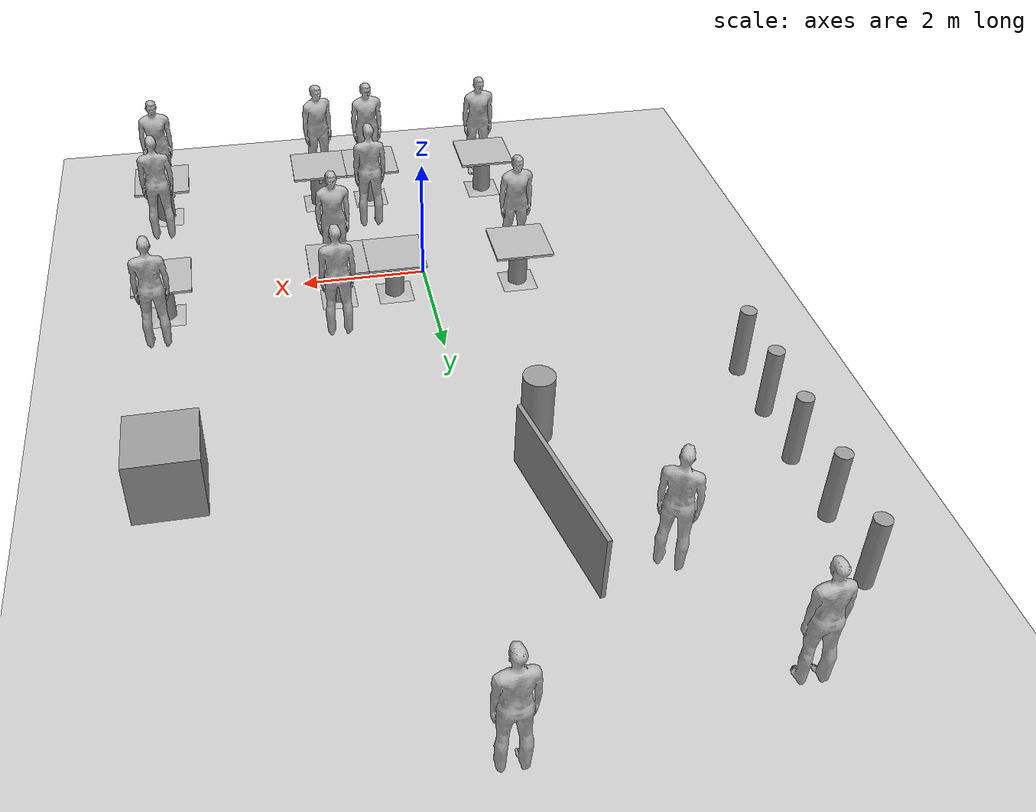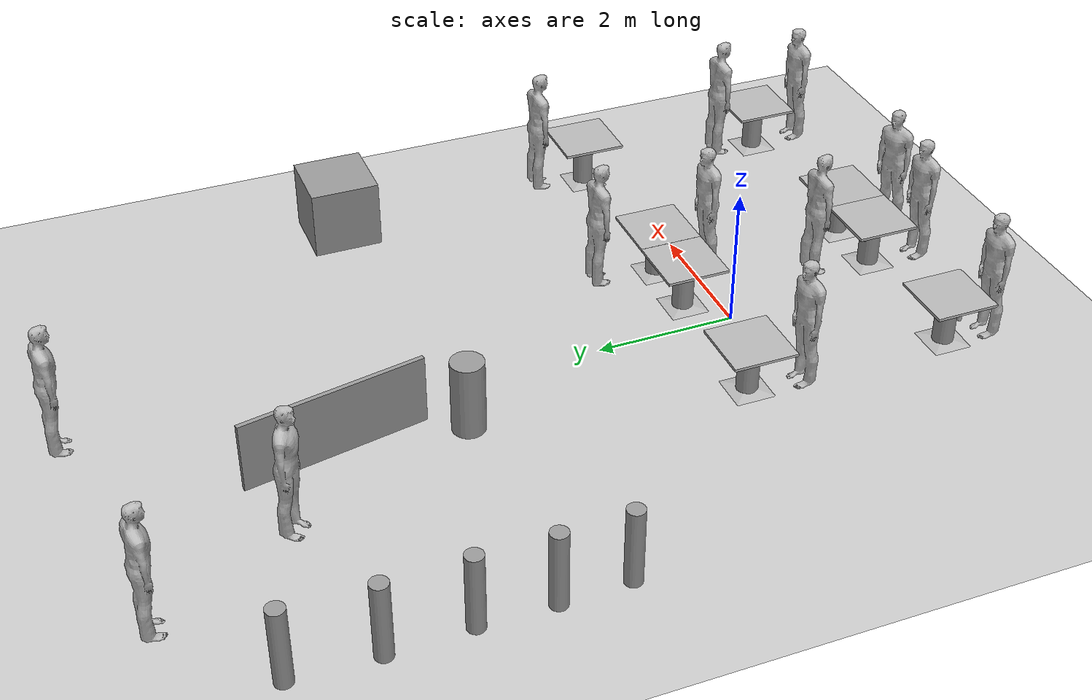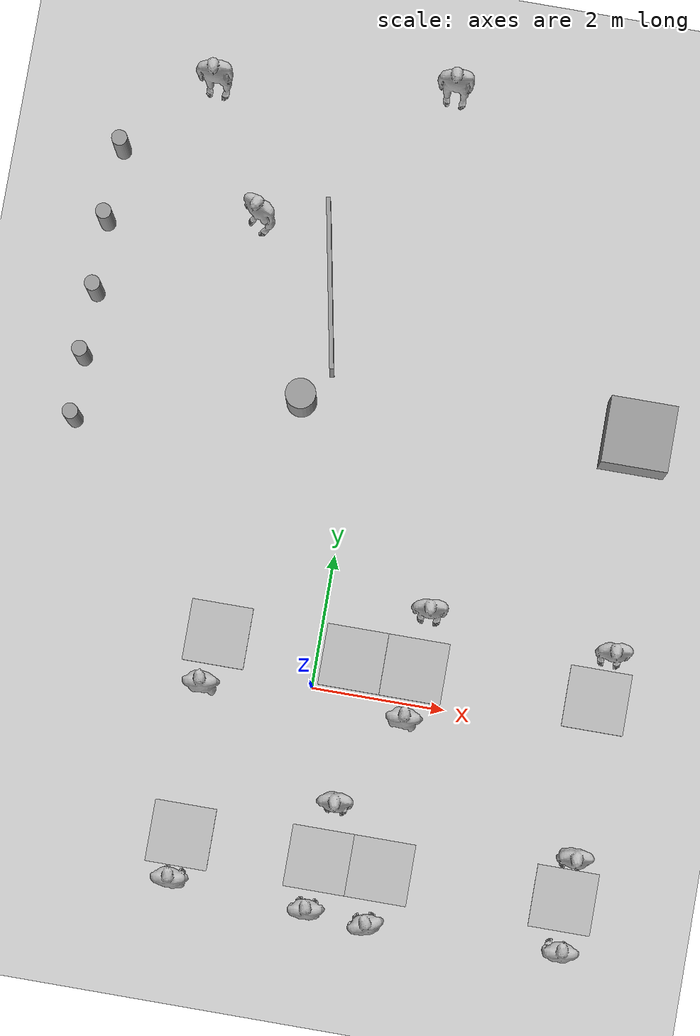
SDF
<sdf version="1.6">
 <world name="default">
  <light name="sun" type="directional">
   <pose>0 0 10 0 -0 0</pose>
   <diffuse>0.8 0.8 0.8 1</diffuse>
   <specular>0.2 0.2 0.2 1</specular>
   <attenuation>
    <range>1000</range>
    <constant>0.9</constant>
    <linear>0.01</linear>
    <quadratic>0.001</quadratic>
   </attenuation>
   <direction>-0.5 0.1 -0.9</direction>
  </light>
  <model name="ground_plane">
   <static>1</static>
   <link name="link">
    <collision name="collision">
     <geometry><plane><normal>0 0 1</normal><size>100 100</size></plane></geometry>
     <surface><friction><ode><mu>100</mu><mu2>50</mu2></ode></friction></surface>
    </collision>
    <visual name="visual">
     <cast_shadows>0</cast_shadows>
     <geometry><plane><normal>0 0 1</normal><size>100 100</size></plane></geometry>
     <material>
      <script><uri>file://media/materials/scripts/gazebo.material</uri><name>Gazebo/Grey</name></script>
     </material>
    </visual>
   </link>
  </model>
  <gravity>0 0 -9.8</gravity>
  <magnetic_field>6e-06 2.3e-05 -4.2e-05</magnetic_field>
  <atmosphere type="adiabatic"/>
  <physics name="default_physics" default="0" type="ode">
   <max_step_size>0.001</max_step_size>
   <real_time_factor>1</real_time_factor>
   <real_time_update_rate>10000</real_time_update_rate>
  </physics>
  <scene><ambient>0.4 0.4 0.4 1</ambient><background>0.7 0.7 0.7 1</background><shadows>1</shadows></scene>
  <spherical_coordinates>
   <surface_model>EARTH_WGS84</surface_model>
   <latitude_deg>0</latitude_deg>
   <longitude_deg>0</longitude_deg>
   <elevation>0</elevation>
   <heading_deg>0</heading_deg>
  </spherical_coordinates>
  <model name="person_standing">
   <link name="link">
    <inertial>
     <pose>0 -0.1 0.95 0 -0 0</pose>
     <mass>80</mass>
     <inertia><ixx>24.88</ixx><ixy>0</ixy><ixz>0</ixz><iyy>25.73</iyy><iyz>0</iyz><izz>2.48</izz></inertia>
    </inertial>
    <collision name="bottom">
     <pose>0 -0.1 0.01 0 -0 0</pose>
     <geometry><box><size>0.5 0.35 0.02</size></box></geometry>
    </collision>
    <collision name="person">
     <pose>0 0 0.02 0.04 -0 0</pose>
     <geometry><mesh><uri>model://person_standing/meshes/standing.dae</uri></mesh></geometry>
    </collision>
    <visual name="visual">
     <pose>0 0 0.02 0.04 -0 0</pose>
     <geometry><mesh><uri>model://person_standing/meshes/standing.dae</uri></mesh></geometry>
    </visual>
   </link>
   <pose>-1.91141 6.86082 -1e-06 -1e-06 1e-06 -0.572801</pose>
  </model>
  <model name="person_standing_0">
   <link name="link">
    <inertial>
     <pose>0 -0.1 0.95 0 -0 0</pose>
     <mass>80</mass>
     <inertia><ixx>24.88</ixx><ixy>0</ixy><ixz>0</ixz><iyy>25.73</iyy><iyz>0</iyz><izz>2.48</izz></inertia>
    </inertial>
    <collision name="bottom">
     <pose>0 -0.1 0.01 0 -0 0</pose>
     <geometry><box><size>0.5 0.35 0.02</size></box></geometry>
    </collision>
    <collision name="person">
     <pose>0 0 0.02 0.04 -0 0</pose>
     <geometry><mesh><uri>model://person_standing/meshes/standing.dae</uri></mesh></geometry>
    </collision>
    <visual name="visual">
     <pose>0 0 0.02 0.04 -0 0</pose>
     <geometry><mesh><uri>model://person_standing/meshes/standing.dae</uri></mesh></geometry>
    </visual>
   </link>
   <pose>0.595831 9.25089 -1e-06 -1e-06 1e-06 -0.001806</pose>
  </model>
  <model name="person_standing_1">
   <link name="link">
    <inertial>
     <pose>0 -0.1 0.95 0 -0 0</pose>
     <mass>80</mass>
     <inertia><ixx>24.88</ixx><ixy>0</ixy><ixz>0</ixz><iyy>25.73</iyy><iyz>0</iyz><izz>2.48</izz></inertia>
    </inertial>
    <collision name="bottom">
     <pose>0 -0.1 0.01 0 -0 0</pose>
     <geometry><box><size>0.5 0.35 0.02</size></box></geometry>
    </collision>
    <collision name="person">
     <pose>0 0 0.02 0.04 -0 0</pose>
     <geometry><mesh><uri>model://person_standing/meshes/standing.dae</uri></mesh></geometry>
    </collision>
    <visual name="visual">
     <pose>0 0 0.02 0.04 -0 0</pose>
     <geometry><mesh><uri>model://person_standing/meshes/standing.dae</uri></mesh></geometry>
    </visual>
   </link>
   <pose>4.29476 1.29139 0 -1e-06 -1e-06 -0.002117</pose>
  </model>
  <model name="person_standing_1_clone">
   <link name="link">
    <inertial>
     <pose>0 -0.1 0.95 0 -0 0</pose>
     <mass>80</mass>
     <inertia><ixx>24.88</ixx><ixy>0</ixy><ixz>0</ixz><iyy>25.73</iyy><iyz>0</iyz><izz>2.48</izz></inertia>
    </inertial>
    <collision name="bottom">
     <pose>0 -0.1 0.01 0 -0 0</pose>
     <geometry><box><size>0.5 0.35 0.02</size></box></geometry>
    </collision>
    <collision name="person">
     <pose>0 0 0.02 0.04 -0 0</pose>
     <geometry><mesh><uri>model://person_standing/meshes/standing.dae</uri></mesh></geometry>
    </collision>
    <visual name="visual">
     <pose>0 0 0.02 0.04 -0 0</pose>
     <geometry><mesh><uri>model://person_standing/meshes/standing.dae</uri></mesh></geometry>
    </visual>
   </link>
   <pose>4.23043 -3.30562 0 1e-06 1e-06 3.12807</pose>
  </model>
  <model name="person_standing_1_clone_0">
   <link name="link">
    <inertial>
     <pose>0 -0.1 0.95 0 -0 0</pose>
     <mass>80</mass>
     <inertia><ixx>24.88</ixx><ixy>0</ixy><ixz>0</ixz><iyy>25.73</iyy><iyz>0</iyz><izz>2.48</izz></inertia>
    </inertial>
    <collision name="bottom">
     <pose>0 -0.1 0.01 0 -0 0</pose>
     <geometry><box><size>0.5 0.35 0.02</size></box></geometry>
    </collision>
    <collision name="person">
     <pose>0 0 0.02 0.04 -0 0</pose>
     <geometry><mesh><uri>model://person_standing/meshes/standing.dae</uri></mesh></geometry>
    </collision>
    <visual name="visual">
     <pose>0 0 0.02 0.04 -0 0</pose>
     <geometry><mesh><uri>model://person_standing/meshes/standing.dae</uri></mesh></geometry>
    </visual>
   </link>
   <pose>1.41682 -0.340179 1e-06 2e-06 -1e-06 3.0977</pose>
  </model>
  <model name="person_standing_1_clone_1">
   <link name="link">
    <inertial>
     <pose>0 -0.1 0.95 0 -0 0</pose>
     <mass>80</mass>
     <inertia><ixx>24.88</ixx><ixy>0</ixy><ixz>0</ixz><iyy>25.73</iyy><iyz>0</iyz><izz>2.48</izz></inertia>
    </inertial>
    <collision name="bottom">
     <pose>0 -0.1 0.01 0 -0 0</pose>
     <geometry><box><size>0.5 0.35 0.02</size></box></geometry>
    </collision>
    <collision name="person">
     <pose>0 0 0.02 0.04 -0 0</pose>
     <geometry><mesh><uri>model://person_standing/meshes/standing.dae</uri></mesh></geometry>
    </collision>
    <visual name="visual">
     <pose>0 0 0.02 0.04 -0 0</pose>
     <geometry><mesh><uri>model://person_standing/meshes/standing.dae</uri></mesh></geometry>
    </visual>
   </link>
   <pose>0.646415 -1.55215 0 0 -1e-06 0.003295</pose>
  </model>
  <model name="person_standing_1_clone_2">
   <link name="link">
    <inertial>
     <pose>0 -0.1 0.95 0 -0 0</pose>
     <mass>80</mass>
     <inertia><ixx>24.88</ixx><ixy>0</ixy><ixz>0</ixz><iyy>25.73</iyy><iyz>0</iyz><izz>2.48</izz></inertia>
    </inertial>
    <collision name="bottom">
     <pose>0 -0.1 0.01 0 -0 0</pose>
     <geometry><box><size>0.5 0.35 0.02</size></box></geometry>
    </collision>
    <collision name="person">
     <pose>0 0 0.02 0.04 -0 0</pose>
     <geometry><mesh><uri>model://person_standing/meshes/standing.dae</uri></mesh></geometry>
    </collision>
    <visual name="visual">
     <pose>0 0 0.02 0.04 -0 0</pose>
     <geometry><mesh><uri>model://person_standing/meshes/standing.dae</uri></mesh></geometry>
    </visual>
   </link>
   <pose>0.490841 -3.32315 0 1e-06 -1e-06 -3.0888</pose>
  </model>
  <model name="person_standing_1_clone_3">
   <link name="link">
    <inertial>
     <pose>0 -0.1 0.95 0 -0 0</pose>
     <mass>80</mass>
     <inertia><ixx>24.88</ixx><ixy>0</ixy><ixz>0</ixz><iyy>25.73</iyy><iyz>0</iyz><izz>2.48</izz></inertia>
    </inertial>
    <collision name="bottom">
     <pose>0 -0.1 0.01 0 -0 0</pose>
     <geometry><box><size>0.5 0.35 0.02</size></box></geometry>
    </collision>
    <collision name="person">
     <pose>0 0 0.02 0.04 -0 0</pose>
     <geometry><mesh><uri>model://person_standing/meshes/standing.dae</uri></mesh></geometry>
    </collision>
    <visual name="visual">
     <pose>0 0 0.02 0.04 -0 0</pose>
     <geometry><mesh><uri>model://person_standing/meshes/standing.dae</uri></mesh></geometry>
    </visual>
   </link>
   <pose>4.22588 -1.76471 0 -1e-06 -1e-06 0.001062</pose>
  </model>
  <model name="person_standing_1_clone_4">
   <link name="link">
    <inertial>
     <pose>0 -0.1 0.95 0 -0 0</pose>
     <mass>80</mass>
     <inertia><ixx>24.88</ixx><ixy>0</ixy><ixz>0</ixz><iyy>25.73</iyy><iyz>0</iyz><izz>2.48</izz></inertia>
    </inertial>
    <collision name="bottom">
     <pose>0 -0.1 0.01 0 -0 0</pose>
     <geometry><box><size>0.5 0.35 0.02</size></box></geometry>
    </collision>
    <collision name="person">
     <pose>0 0 0.02 0.04 -0 0</pose>
     <geometry><mesh><uri>model://person_standing/meshes/standing.dae</uri></mesh></geometry>
    </collision>
    <visual name="visual">
     <pose>0 0 0.02 0.04 -0 0</pose>
     <geometry><mesh><uri>model://person_standing/meshes/standing.dae</uri></mesh></geometry>
    </visual>
   </link>
   <pose>1.4013 -3.38995 0 0 1e-06 -2.84646</pose>
  </model>
  <model name="person_standing_1_clone_5">
   <link name="link">
    <inertial>
     <pose>0 -0.1 0.95 0 -0 0</pose>
     <mass>80</mass>
     <inertia><ixx>24.88</ixx><ixy>0</ixy><ixz>0</ixz><iyy>25.73</iyy><iyz>0</iyz><izz>2.48</izz></inertia>
    </inertial>
    <collision name="bottom">
     <pose>0 -0.1 0.01 0 -0 0</pose>
     <geometry><box><size>0.5 0.35 0.02</size></box></geometry>
    </collision>
    <collision name="person">
     <pose>0 0 0.02 0.04 -0 0</pose>
     <geometry><mesh><uri>model://person_standing/meshes/standing.dae</uri></mesh></geometry>
    </collision>
    <visual name="visual">
     <pose>0 0 0.02 0.04 -0 0</pose>
     <geometry><mesh><uri>model://person_standing/meshes/standing.dae</uri></mesh></geometry>
    </visual>
   </link>
   <pose>1.53594 1.46348 0 1e-06 1e-06 -0.002811</pose>
  </model>
  <model name="person_standing_1_clone_6">
   <link name="link">
    <inertial>
     <pose>0 -0.1 0.95 0 -0 0</pose>
     <mass>80</mass>
     <inertia><ixx>24.88</ixx><ixy>0</ixy><ixz>0</ixz><iyy>25.73</iyy><iyz>0</iyz><izz>2.48</izz></inertia>
    </inertial>
    <collision name="bottom">
     <pose>0 -0.1 0.01 0 -0 0</pose>
     <geometry><box><size>0.5 0.35 0.02</size></box></geometry>
    </collision>
    <collision name="person">
     <pose>0 0 0.02 0.04 -0 0</pose>
     <geometry><mesh><uri>model://person_standing/meshes/standing.dae</uri></mesh></geometry>
    </collision>
    <visual name="visual">
     <pose>0 0 0.02 0.04 -0 0</pose>
     <geometry><mesh><uri>model://person_standing/meshes/standing.dae</uri></mesh></geometry>
    </visual>
   </link>
   <pose>-1.58943 -0.320175 -1e-06 -1e-06 1e-06 -3.12397</pose>
  </model>
  <model name="person_standing_1_clone_7">
   <link name="link">
    <inertial>
     <pose>0 -0.1 0.95 0 -0 0</pose>
     <mass>80</mass>
     <inertia><ixx>24.88</ixx><ixy>0</ixy><ixz>0</ixz><iyy>25.73</iyy><iyz>0</iyz><izz>2.48</izz></inertia>
    </inertial>
    <collision name="bottom">
     <pose>0 -0.1 0.01 0 -0 0</pose>
     <geometry><box><size>0.5 0.35 0.02</size></box></geometry>
    </collision>
    <collision name="person">
     <pose>0 0 0.02 0.04 -0 0</pose>
     <geometry><mesh><uri>model://person_standing/meshes/standing.dae</uri></mesh></geometry>
    </collision>
    <visual name="visual">
     <pose>0 0 0.02 0.04 -0 0</pose>
     <geometry><mesh><uri>model://person_standing/meshes/standing.dae</uri></mesh></geometry>
    </visual>
   </link>
   <pose>-1.54717 -3.20367 -1e-06 -1e-06 1e-06 3.12525</pose>
  </model>
  <model name="cafe_table_clone_4">
   <link name="link">
    <visual name="visual">
     <geometry><mesh><uri>model://cafe_table/meshes/cafe_table.dae</uri></mesh></geometry>
     <material><shader type="pixel"/><emissive>0 0 0 1</emissive></material>
    </visual>
    <collision name="surface">
     <pose>0 0 0.755 0 -0 0</pose>
     <geometry><box><size>0.913 0.913 0.04</size></box></geometry>
     <surface>
      <friction>
       <ode><mu>1</mu><mu2>1</mu2><fdir1>0 0 0</fdir1><slip1>0</slip1><slip2>0</slip2></ode>
       <torsional>
        <coefficient>1</coefficient>
        <patch_radius>0</patch_radius>
        <surface_radius>0</surface_radius>
        <use_patch_radius>1</use_patch_radius>
        <ode><slip>0</slip></ode>
       </torsional>
      </friction>
      <bounce><restitution_coefficient>0</restitution_coefficient><threshold>1e+06</threshold></bounce>
      <contact>
       <collide_without_contact>0</collide_without_contact>
       <collide_without_contact_bitmask>1</collide_without_contact_bitmask>
       <collide_bitmask>1</collide_bitmask>
       <ode>
        <soft_cfm>0</soft_cfm>
        <soft_erp>0.2</soft_erp>
        <kp>1e+13</kp>
        <kd>1</kd>
        <max_vel>0.01</max_vel>
        <min_depth>0</min_depth>
       </ode>
       <bullet>
        <split_impulse>1</split_impulse>
        <split_impulse_penetration_threshold>-0.01</split_impulse_penetration_threshold>
        <soft_cfm>0</soft_cfm>
        <soft_erp>0.2</soft_erp>
        <kp>1e+13</kp>
        <kd>1</kd>
       </bullet>
      </contact>
     </surface>
    </collision>
    <collision name="column">
     <pose>0 0 0.37 0 -0 0</pose>
     <geometry><box><size>0.042 0.042 0.74</size></box></geometry>
     <surface>
      <friction>
       <ode><mu>1</mu><mu2>1</mu2><fdir1>0 0 0</fdir1><slip1>0</slip1><slip2>0</slip2></ode>
       <torsional>
        <coefficient>1</coefficient>
        <patch_radius>0</patch_radius>
        <surface_radius>0</surface_radius>
        <use_patch_radius>1</use_patch_radius>
        <ode><slip>0</slip></ode>
       </torsional>
      </friction>
      <bounce><restitution_coefficient>0</restitution_coefficient><threshold>1e+06</threshold></bounce>
      <contact>
       <collide_without_contact>0</collide_without_contact>
       <collide_without_contact_bitmask>1</collide_without_contact_bitmask>
       <collide_bitmask>1</collide_bitmask>
       <ode>
        <soft_cfm>0</soft_cfm>
        <soft_erp>0.2</soft_erp>
        <kp>1e+13</kp>
        <kd>1</kd>
        <max_vel>0.01</max_vel>
        <min_depth>0</min_depth>
       </ode>
       <bullet>
        <split_impulse>1</split_impulse>
        <split_impulse_penetration_threshold>-0.01</split_impulse_penetration_threshold>
        <soft_cfm>0</soft_cfm>
        <soft_erp>0.2</soft_erp>
        <kp>1e+13</kp>
        <kd>1</kd>
       </bullet>
      </contact>
     </surface>
    </collision>
    <collision name="base">
     <pose>0 0 0.02 0 -0 0</pose>
     <geometry><box><size>0.56 0.56 0.04</size></box></geometry>
     <surface>
      <friction>
       <ode><mu>1</mu><mu2>1</mu2><fdir1>0 0 0</fdir1><slip1>0</slip1><slip2>0</slip2></ode>
       <torsional>
        <coefficient>1</coefficient>
        <patch_radius>0</patch_radius>
        <surface_radius>0</surface_radius>
        <use_patch_radius>1</use_patch_radius>
        <ode><slip>0</slip></ode>
       </torsional>
      </friction>
      <bounce><restitution_coefficient>0</restitution_coefficient><threshold>1e+06</threshold></bounce>
      <contact>
       <collide_without_contact>0</collide_without_contact>
       <collide_without_contact_bitmask>1</collide_without_contact_bitmask>
       <collide_bitmask>1</collide_bitmask>
       <ode>
        <soft_cfm>0</soft_cfm>
        <soft_erp>0.2</soft_erp>
        <kp>1e+13</kp>
        <kd>1</kd>
        <max_vel>0.01</max_vel>
        <min_depth>0</min_depth>
       </ode>
       <bullet>
        <split_impulse>1</split_impulse>
        <split_impulse_penetration_threshold>-0.01</split_impulse_penetration_threshold>
        <soft_cfm>0</soft_cfm>
        <soft_erp>0.2</soft_erp>
        <kp>1e+13</kp>
        <kd>1</kd>
       </bullet>
      </contact>
     </surface>
    </collision>
   </link>
   <link name="link_1">
    <pose>0.006591 0.003726 0.34636 0 -0 0</pose>
    <inertial>
     <mass>0.0583743</mass>
     <inertia>
      <ixx>0.00238915</ixx>
      <ixy>0</ixy>
      <ixz>0</ixz>
      <iyy>0.00238915</iyy>
      <iyz>0</iyz>
      <izz>0.000654099</izz>
     </inertia>
    </inertial>
    <visual name="visual">
     <geometry><cylinder><radius>0.149701</radius><length>0.65108</length></cylinder></geometry>
     <material>
      <lighting>1</lighting>
      <script><uri>file://media/materials/scripts/gazebo.material</uri><name>Gazebo/Grey</name></script>
      <shader type="pixel"/>
      <ambient>0.3 0.3 0.3 1</ambient>
      <diffuse>0.7 0.7 0.7 1</diffuse>
      <specular>0.01 0.01 0.01 1</specular>
      <emissive>0 0 0 1</emissive>
     </material>
    </visual>
    <collision name="collision">
     <geometry><cylinder><radius>0.149701</radius><length>0.65108</length></cylinder></geometry>
     <surface>
      <friction>
       <ode><mu>1</mu><mu2>1</mu2><fdir1>0 0 0</fdir1><slip1>0</slip1><slip2>0</slip2></ode>
       <torsional>
        <coefficient>1</coefficient>
        <patch_radius>0</patch_radius>
        <surface_radius>0</surface_radius>
        <use_patch_radius>1</use_patch_radius>
        <ode><slip>0</slip></ode>
       </torsional>
      </friction>
      <bounce><restitution_coefficient>0</restitution_coefficient><threshold>1e+06</threshold></bounce>
      <contact>
       <collide_without_contact>0</collide_without_contact>
       <collide_without_contact_bitmask>1</collide_without_contact_bitmask>
       <collide_bitmask>1</collide_bitmask>
       <ode>
        <soft_cfm>0</soft_cfm>
        <soft_erp>0.2</soft_erp>
        <kp>1e+13</kp>
        <kd>1</kd>
        <max_vel>0.01</max_vel>
        <min_depth>0</min_depth>
       </ode>
       <bullet>
        <split_impulse>1</split_impulse>
        <split_impulse_penetration_threshold>-0.01</split_impulse_penetration_threshold>
        <soft_cfm>0</soft_cfm>
        <soft_erp>0.2</soft_erp>
        <kp>1e+13</kp>
        <kd>1</kd>
       </bullet>
      </contact>
     </surface>
    </collision>
   </link>
   <joint name="link_JOINT_0" type="revolute">
    <parent>link</parent>
    <child>link_1</child>
    <axis>
     <xyz>1 0 0</xyz>
     <use_parent_model_frame>0</use_parent_model_frame>
     <limit>
      <lower>-1.79769e+308</lower>
      <upper>1.79769e+308</upper>
      <effort>-1</effort>
      <velocity>-1</velocity>
     </limit>
     <dynamics>
      <spring_reference>0</spring_reference>
      <spring_stiffness>0</spring_stiffness>
      <damping>0</damping>
     </dynamics>
    </axis>
    <physics>
     <ode><limit><cfm>0</cfm><erp>0.2</erp></limit><suspension><cfm>0</cfm><erp>0.2</erp></suspension></ode>
    </physics>
   </joint>
   <static>1</static>
   <pose>-1.48825 0.511063 0 0 -0 0</pose>
  </model>
  <model name="cafe_table_clone_4_clone">
   <link name="link">
    <visual name="visual">
     <geometry><mesh><uri>model://cafe_table/meshes/cafe_table.dae</uri></mesh></geometry>
     <material><shader type="pixel"/><emissive>0 0 0 1</emissive></material>
    </visual>
    <collision name="surface">
     <pose>0 0 0.755 0 -0 0</pose>
     <geometry><box><size>0.913 0.913 0.04</size></box></geometry>
     <surface>
      <friction>
       <ode><mu>1</mu><mu2>1</mu2><fdir1>0 0 0</fdir1><slip1>0</slip1><slip2>0</slip2></ode>
       <torsional>
        <coefficient>1</coefficient>
        <patch_radius>0</patch_radius>
        <surface_radius>0</surface_radius>
        <use_patch_radius>1</use_patch_radius>
        <ode><slip>0</slip></ode>
       </torsional>
      </friction>
      <bounce><restitution_coefficient>0</restitution_coefficient><threshold>1e+06</threshold></bounce>
      <contact>
       <collide_without_contact>0</collide_without_contact>
       <collide_without_contact_bitmask>1</collide_without_contact_bitmask>
       <collide_bitmask>1</collide_bitmask>
       <ode>
        <soft_cfm>0</soft_cfm>
        <soft_erp>0.2</soft_erp>
        <kp>1e+13</kp>
        <kd>1</kd>
        <max_vel>0.01</max_vel>
        <min_depth>0</min_depth>
       </ode>
       <bullet>
        <split_impulse>1</split_impulse>
        <split_impulse_penetration_threshold>-0.01</split_impulse_penetration_threshold>
        <soft_cfm>0</soft_cfm>
        <soft_erp>0.2</soft_erp>
        <kp>1e+13</kp>
        <kd>1</kd>
       </bullet>
      </contact>
     </surface>
    </collision>
    <collision name="column">
     <pose>0 0 0.37 0 -0 0</pose>
     <geometry><box><size>0.042 0.042 0.74</size></box></geometry>
     <surface>
      <friction>
       <ode><mu>1</mu><mu2>1</mu2><fdir1>0 0 0</fdir1><slip1>0</slip1><slip2>0</slip2></ode>
       <torsional>
        <coefficient>1</coefficient>
        <patch_radius>0</patch_radius>
        <surface_radius>0</surface_radius>
        <use_patch_radius>1</use_patch_radius>
        <ode><slip>0</slip></ode>
       </torsional>
      </friction>
      <bounce><restitution_coefficient>0</restitution_coefficient><threshold>1e+06</threshold></bounce>
      <contact>
       <collide_without_contact>0</collide_without_contact>
       <collide_without_contact_bitmask>1</collide_without_contact_bitmask>
       <collide_bitmask>1</collide_bitmask>
       <ode>
        <soft_cfm>0</soft_cfm>
        <soft_erp>0.2</soft_erp>
        <kp>1e+13</kp>
        <kd>1</kd>
        <max_vel>0.01</max_vel>
        <min_depth>0</min_depth>
       </ode>
       <bullet>
        <split_impulse>1</split_impulse>
        <split_impulse_penetration_threshold>-0.01</split_impulse_penetration_threshold>
        <soft_cfm>0</soft_cfm>
        <soft_erp>0.2</soft_erp>
        <kp>1e+13</kp>
        <kd>1</kd>
       </bullet>
      </contact>
     </surface>
    </collision>
    <collision name="base">
     <pose>0 0 0.02 0 -0 0</pose>
     <geometry><box><size>0.56 0.56 0.04</size></box></geometry>
     <surface>
      <friction>
       <ode><mu>1</mu><mu2>1</mu2><fdir1>0 0 0</fdir1><slip1>0</slip1><slip2>0</slip2></ode>
       <torsional>
        <coefficient>1</coefficient>
        <patch_radius>0</patch_radius>
        <surface_radius>0</surface_radius>
        <use_patch_radius>1</use_patch_radius>
        <ode><slip>0</slip></ode>
       </torsional>
      </friction>
      <bounce><restitution_coefficient>0</restitution_coefficient><threshold>1e+06</threshold></bounce>
      <contact>
       <collide_without_contact>0</collide_without_contact>
       <collide_without_contact_bitmask>1</collide_without_contact_bitmask>
       <collide_bitmask>1</collide_bitmask>
       <ode>
        <soft_cfm>0</soft_cfm>
        <soft_erp>0.2</soft_erp>
        <kp>1e+13</kp>
        <kd>1</kd>
        <max_vel>0.01</max_vel>
        <min_depth>0</min_depth>
       </ode>
       <bullet>
        <split_impulse>1</split_impulse>
        <split_impulse_penetration_threshold>-0.01</split_impulse_penetration_threshold>
        <soft_cfm>0</soft_cfm>
        <soft_erp>0.2</soft_erp>
        <kp>1e+13</kp>
        <kd>1</kd>
       </bullet>
      </contact>
     </surface>
    </collision>
   </link>
   <link name="link_1">
    <pose>0.006591 0.003726 0.34636 0 -0 0</pose>
    <inertial>
     <mass>0.0583743</mass>
     <inertia>
      <ixx>0.00238915</ixx>
      <ixy>0</ixy>
      <ixz>0</ixz>
      <iyy>0.00238915</iyy>
      <iyz>0</iyz>
      <izz>0.000654099</izz>
     </inertia>
    </inertial>
    <visual name="visual">
     <geometry><cylinder><radius>0.149701</radius><length>0.65108</length></cylinder></geometry>
     <material>
      <lighting>1</lighting>
      <script><uri>file://media/materials/scripts/gazebo.material</uri><name>Gazebo/Grey</name></script>
      <shader type="pixel"/>
      <ambient>0.3 0.3 0.3 1</ambient>
      <diffuse>0.7 0.7 0.7 1</diffuse>
      <specular>0.01 0.01 0.01 1</specular>
      <emissive>0 0 0 1</emissive>
     </material>
    </visual>
    <collision name="collision">
     <geometry><cylinder><radius>0.149701</radius><length>0.65108</length></cylinder></geometry>
     <surface>
      <friction>
       <ode><mu>1</mu><mu2>1</mu2><fdir1>0 0 0</fdir1><slip1>0</slip1><slip2>0</slip2></ode>
       <torsional>
        <coefficient>1</coefficient>
        <patch_radius>0</patch_radius>
        <surface_radius>0</surface_radius>
        <use_patch_radius>1</use_patch_radius>
        <ode><slip>0</slip></ode>
       </torsional>
      </friction>
      <bounce><restitution_coefficient>0</restitution_coefficient><threshold>1e+06</threshold></bounce>
      <contact>
       <collide_without_contact>0</collide_without_contact>
       <collide_without_contact_bitmask>1</collide_without_contact_bitmask>
       <collide_bitmask>1</collide_bitmask>
       <ode>
        <soft_cfm>0</soft_cfm>
        <soft_erp>0.2</soft_erp>
        <kp>1e+13</kp>
        <kd>1</kd>
        <max_vel>0.01</max_vel>
        <min_depth>0</min_depth>
       </ode>
       <bullet>
        <split_impulse>1</split_impulse>
        <split_impulse_penetration_threshold>-0.01</split_impulse_penetration_threshold>
        <soft_cfm>0</soft_cfm>
        <soft_erp>0.2</soft_erp>
        <kp>1e+13</kp>
        <kd>1</kd>
       </bullet>
      </contact>
     </surface>
    </collision>
   </link>
   <joint name="link_JOINT_0" type="revolute">
    <parent>link</parent>
    <child>link_1</child>
    <axis>
     <xyz>1 0 0</xyz>
     <use_parent_model_frame>0</use_parent_model_frame>
     <limit>
      <lower>-1.79769e+308</lower>
      <upper>1.79769e+308</upper>
      <effort>-1</effort>
      <velocity>-1</velocity>
     </limit>
     <dynamics>
      <spring_reference>0</spring_reference>
      <spring_stiffness>0</spring_stiffness>
      <damping>0</damping>
     </dynamics>
    </axis>
    <physics>
     <ode><limit><cfm>0</cfm><erp>0.2</erp></limit><suspension><cfm>0</cfm><erp>0.2</erp></suspension></ode>
    </physics>
   </joint>
   <static>1</static>
   <pose>0.543995 0.489415 0 0 -0 0</pose>
  </model>
  <model name="cafe_table_clone_4_clone_0">
   <link name="link">
    <visual name="visual">
     <geometry><mesh><uri>model://cafe_table/meshes/cafe_table.dae</uri></mesh></geometry>
     <material><shader type="pixel"/><emissive>0 0 0 1</emissive></material>
    </visual>
    <collision name="surface">
     <pose>0 0 0.755 0 -0 0</pose>
     <geometry><box><size>0.913 0.913 0.04</size></box></geometry>
     <surface>
      <friction>
       <ode><mu>1</mu><mu2>1</mu2><fdir1>0 0 0</fdir1><slip1>0</slip1><slip2>0</slip2></ode>
       <torsional>
        <coefficient>1</coefficient>
        <patch_radius>0</patch_radius>
        <surface_radius>0</surface_radius>
        <use_patch_radius>1</use_patch_radius>
        <ode><slip>0</slip></ode>
       </torsional>
      </friction>
      <bounce><restitution_coefficient>0</restitution_coefficient><threshold>1e+06</threshold></bounce>
      <contact>
       <collide_without_contact>0</collide_without_contact>
       <collide_without_contact_bitmask>1</collide_without_contact_bitmask>
       <collide_bitmask>1</collide_bitmask>
       <ode>
        <soft_cfm>0</soft_cfm>
        <soft_erp>0.2</soft_erp>
        <kp>1e+13</kp>
        <kd>1</kd>
        <max_vel>0.01</max_vel>
        <min_depth>0</min_depth>
       </ode>
       <bullet>
        <split_impulse>1</split_impulse>
        <split_impulse_penetration_threshold>-0.01</split_impulse_penetration_threshold>
        <soft_cfm>0</soft_cfm>
        <soft_erp>0.2</soft_erp>
        <kp>1e+13</kp>
        <kd>1</kd>
       </bullet>
      </contact>
     </surface>
    </collision>
    <collision name="column">
     <pose>0 0 0.37 0 -0 0</pose>
     <geometry><box><size>0.042 0.042 0.74</size></box></geometry>
     <surface>
      <friction>
       <ode><mu>1</mu><mu2>1</mu2><fdir1>0 0 0</fdir1><slip1>0</slip1><slip2>0</slip2></ode>
       <torsional>
        <coefficient>1</coefficient>
        <patch_radius>0</patch_radius>
        <surface_radius>0</surface_radius>
        <use_patch_radius>1</use_patch_radius>
        <ode><slip>0</slip></ode>
       </torsional>
      </friction>
      <bounce><restitution_coefficient>0</restitution_coefficient><threshold>1e+06</threshold></bounce>
      <contact>
       <collide_without_contact>0</collide_without_contact>
       <collide_without_contact_bitmask>1</collide_without_contact_bitmask>
       <collide_bitmask>1</collide_bitmask>
       <ode>
        <soft_cfm>0</soft_cfm>
        <soft_erp>0.2</soft_erp>
        <kp>1e+13</kp>
        <kd>1</kd>
        <max_vel>0.01</max_vel>
        <min_depth>0</min_depth>
       </ode>
       <bullet>
        <split_impulse>1</split_impulse>
        <split_impulse_penetration_threshold>-0.01</split_impulse_penetration_threshold>
        <soft_cfm>0</soft_cfm>
        <soft_erp>0.2</soft_erp>
        <kp>1e+13</kp>
        <kd>1</kd>
       </bullet>
      </contact>
     </surface>
    </collision>
    <collision name="base">
     <pose>0 0 0.02 0 -0 0</pose>
     <geometry><box><size>0.56 0.56 0.04</size></box></geometry>
     <surface>
      <friction>
       <ode><mu>1</mu><mu2>1</mu2><fdir1>0 0 0</fdir1><slip1>0</slip1><slip2>0</slip2></ode>
       <torsional>
        <coefficient>1</coefficient>
        <patch_radius>0</patch_radius>
        <surface_radius>0</surface_radius>
        <use_patch_radius>1</use_patch_radius>
        <ode><slip>0</slip></ode>
       </torsional>
      </friction>
      <bounce><restitution_coefficient>0</restitution_coefficient><threshold>1e+06</threshold></bounce>
      <contact>
       <collide_without_contact>0</collide_without_contact>
       <collide_without_contact_bitmask>1</collide_without_contact_bitmask>
       <collide_bitmask>1</collide_bitmask>
       <ode>
        <soft_cfm>0</soft_cfm>
        <soft_erp>0.2</soft_erp>
        <kp>1e+13</kp>
        <kd>1</kd>
        <max_vel>0.01</max_vel>
        <min_depth>0</min_depth>
       </ode>
       <bullet>
        <split_impulse>1</split_impulse>
        <split_impulse_penetration_threshold>-0.01</split_impulse_penetration_threshold>
        <soft_cfm>0</soft_cfm>
        <soft_erp>0.2</soft_erp>
        <kp>1e+13</kp>
        <kd>1</kd>
       </bullet>
      </contact>
     </surface>
    </collision>
   </link>
   <link name="link_1">
    <pose>0.006591 0.003726 0.34636 0 -0 0</pose>
    <inertial>
     <mass>0.0583743</mass>
     <inertia>
      <ixx>0.00238915</ixx>
      <ixy>0</ixy>
      <ixz>0</ixz>
      <iyy>0.00238915</iyy>
      <iyz>0</iyz>
      <izz>0.000654099</izz>
     </inertia>
    </inertial>
    <visual name="visual">
     <geometry><cylinder><radius>0.149701</radius><length>0.65108</length></cylinder></geometry>
     <material>
      <lighting>1</lighting>
      <script><uri>file://media/materials/scripts/gazebo.material</uri><name>Gazebo/Grey</name></script>
      <shader type="pixel"/>
      <ambient>0.3 0.3 0.3 1</ambient>
      <diffuse>0.7 0.7 0.7 1</diffuse>
      <specular>0.01 0.01 0.01 1</specular>
      <emissive>0 0 0 1</emissive>
     </material>
    </visual>
    <collision name="collision">
     <geometry><cylinder><radius>0.149701</radius><length>0.65108</length></cylinder></geometry>
     <surface>
      <friction>
       <ode><mu>1</mu><mu2>1</mu2><fdir1>0 0 0</fdir1><slip1>0</slip1><slip2>0</slip2></ode>
       <torsional>
        <coefficient>1</coefficient>
        <patch_radius>0</patch_radius>
        <surface_radius>0</surface_radius>
        <use_patch_radius>1</use_patch_radius>
        <ode><slip>0</slip></ode>
       </torsional>
      </friction>
      <bounce><restitution_coefficient>0</restitution_coefficient><threshold>1e+06</threshold></bounce>
      <contact>
       <collide_without_contact>0</collide_without_contact>
       <collide_without_contact_bitmask>1</collide_without_contact_bitmask>
       <collide_bitmask>1</collide_bitmask>
       <ode>
        <soft_cfm>0</soft_cfm>
        <soft_erp>0.2</soft_erp>
        <kp>1e+13</kp>
        <kd>1</kd>
        <max_vel>0.01</max_vel>
        <min_depth>0</min_depth>
       </ode>
       <bullet>
        <split_impulse>1</split_impulse>
        <split_impulse_penetration_threshold>-0.01</split_impulse_penetration_threshold>
        <soft_cfm>0</soft_cfm>
        <soft_erp>0.2</soft_erp>
        <kp>1e+13</kp>
        <kd>1</kd>
       </bullet>
      </contact>
     </surface>
    </collision>
   </link>
   <joint name="link_JOINT_0" type="revolute">
    <parent>link</parent>
    <child>link_1</child>
    <axis>
     <xyz>1 0 0</xyz>
     <use_parent_model_frame>0</use_parent_model_frame>
     <limit>
      <lower>-1.79769e+308</lower>
      <upper>1.79769e+308</upper>
      <effort>-1</effort>
      <velocity>-1</velocity>
     </limit>
     <dynamics>
      <spring_reference>0</spring_reference>
      <spring_stiffness>0</spring_stiffness>
      <damping>0</damping>
     </dynamics>
    </axis>
    <physics>
     <ode><limit><cfm>0</cfm><erp>0.2</erp></limit><suspension><cfm>0</cfm><erp>0.2</erp></suspension></ode>
    </physics>
   </joint>
   <static>1</static>
   <pose>1.46012 0.488325 0 0 -0 0</pose>
  </model>
  <model name="cafe_table_clone_4_clone_1">
   <link name="link">
    <visual name="visual">
     <geometry><mesh><uri>model://cafe_table/meshes/cafe_table.dae</uri></mesh></geometry>
     <material><shader type="pixel"/><emissive>0 0 0 1</emissive></material>
    </visual>
    <collision name="surface">
     <pose>0 0 0.755 0 -0 0</pose>
     <geometry><box><size>0.913 0.913 0.04</size></box></geometry>
     <surface>
      <friction>
       <ode><mu>1</mu><mu2>1</mu2><fdir1>0 0 0</fdir1><slip1>0</slip1><slip2>0</slip2></ode>
       <torsional>
        <coefficient>1</coefficient>
        <patch_radius>0</patch_radius>
        <surface_radius>0</surface_radius>
        <use_patch_radius>1</use_patch_radius>
        <ode><slip>0</slip></ode>
       </torsional>
      </friction>
      <bounce><restitution_coefficient>0</restitution_coefficient><threshold>1e+06</threshold></bounce>
      <contact>
       <collide_without_contact>0</collide_without_contact>
       <collide_without_contact_bitmask>1</collide_without_contact_bitmask>
       <collide_bitmask>1</collide_bitmask>
       <ode>
        <soft_cfm>0</soft_cfm>
        <soft_erp>0.2</soft_erp>
        <kp>1e+13</kp>
        <kd>1</kd>
        <max_vel>0.01</max_vel>
        <min_depth>0</min_depth>
       </ode>
       <bullet>
        <split_impulse>1</split_impulse>
        <split_impulse_penetration_threshold>-0.01</split_impulse_penetration_threshold>
        <soft_cfm>0</soft_cfm>
        <soft_erp>0.2</soft_erp>
        <kp>1e+13</kp>
        <kd>1</kd>
       </bullet>
      </contact>
     </surface>
    </collision>
    <collision name="column">
     <pose>0 0 0.37 0 -0 0</pose>
     <geometry><box><size>0.042 0.042 0.74</size></box></geometry>
     <surface>
      <friction>
       <ode><mu>1</mu><mu2>1</mu2><fdir1>0 0 0</fdir1><slip1>0</slip1><slip2>0</slip2></ode>
       <torsional>
        <coefficient>1</coefficient>
        <patch_radius>0</patch_radius>
        <surface_radius>0</surface_radius>
        <use_patch_radius>1</use_patch_radius>
        <ode><slip>0</slip></ode>
       </torsional>
      </friction>
      <bounce><restitution_coefficient>0</restitution_coefficient><threshold>1e+06</threshold></bounce>
      <contact>
       <collide_without_contact>0</collide_without_contact>
       <collide_without_contact_bitmask>1</collide_without_contact_bitmask>
       <collide_bitmask>1</collide_bitmask>
       <ode>
        <soft_cfm>0</soft_cfm>
        <soft_erp>0.2</soft_erp>
        <kp>1e+13</kp>
        <kd>1</kd>
        <max_vel>0.01</max_vel>
        <min_depth>0</min_depth>
       </ode>
       <bullet>
        <split_impulse>1</split_impulse>
        <split_impulse_penetration_threshold>-0.01</split_impulse_penetration_threshold>
        <soft_cfm>0</soft_cfm>
        <soft_erp>0.2</soft_erp>
        <kp>1e+13</kp>
        <kd>1</kd>
       </bullet>
      </contact>
     </surface>
    </collision>
    <collision name="base">
     <pose>0 0 0.02 0 -0 0</pose>
     <geometry><box><size>0.56 0.56 0.04</size></box></geometry>
     <surface>
      <friction>
       <ode><mu>1</mu><mu2>1</mu2><fdir1>0 0 0</fdir1><slip1>0</slip1><slip2>0</slip2></ode>
       <torsional>
        <coefficient>1</coefficient>
        <patch_radius>0</patch_radius>
        <surface_radius>0</surface_radius>
        <use_patch_radius>1</use_patch_radius>
        <ode><slip>0</slip></ode>
       </torsional>
      </friction>
      <bounce><restitution_coefficient>0</restitution_coefficient><threshold>1e+06</threshold></bounce>
      <contact>
       <collide_without_contact>0</collide_without_contact>
       <collide_without_contact_bitmask>1</collide_without_contact_bitmask>
       <collide_bitmask>1</collide_bitmask>
       <ode>
        <soft_cfm>0</soft_cfm>
        <soft_erp>0.2</soft_erp>
        <kp>1e+13</kp>
        <kd>1</kd>
        <max_vel>0.01</max_vel>
        <min_depth>0</min_depth>
       </ode>
       <bullet>
        <split_impulse>1</split_impulse>
        <split_impulse_penetration_threshold>-0.01</split_impulse_penetration_threshold>
        <soft_cfm>0</soft_cfm>
        <soft_erp>0.2</soft_erp>
        <kp>1e+13</kp>
        <kd>1</kd>
       </bullet>
      </contact>
     </surface>
    </collision>
   </link>
   <link name="link_1">
    <pose>0.006591 0.003726 0.34636 0 -0 0</pose>
    <inertial>
     <mass>0.0583743</mass>
     <inertia>
      <ixx>0.00238915</ixx>
      <ixy>0</ixy>
      <ixz>0</ixz>
      <iyy>0.00238915</iyy>
      <iyz>0</iyz>
      <izz>0.000654099</izz>
     </inertia>
    </inertial>
    <visual name="visual">
     <geometry><cylinder><radius>0.149701</radius><length>0.65108</length></cylinder></geometry>
     <material>
      <lighting>1</lighting>
      <script><uri>file://media/materials/scripts/gazebo.material</uri><name>Gazebo/Grey</name></script>
      <shader type="pixel"/>
      <ambient>0.3 0.3 0.3 1</ambient>
      <diffuse>0.7 0.7 0.7 1</diffuse>
      <specular>0.01 0.01 0.01 1</specular>
      <emissive>0 0 0 1</emissive>
     </material>
    </visual>
    <collision name="collision">
     <geometry><cylinder><radius>0.149701</radius><length>0.65108</length></cylinder></geometry>
     <surface>
      <friction>
       <ode><mu>1</mu><mu2>1</mu2><fdir1>0 0 0</fdir1><slip1>0</slip1><slip2>0</slip2></ode>
       <torsional>
        <coefficient>1</coefficient>
        <patch_radius>0</patch_radius>
        <surface_radius>0</surface_radius>
        <use_patch_radius>1</use_patch_radius>
        <ode><slip>0</slip></ode>
       </torsional>
      </friction>
      <bounce><restitution_coefficient>0</restitution_coefficient><threshold>1e+06</threshold></bounce>
      <contact>
       <collide_without_contact>0</collide_without_contact>
       <collide_without_contact_bitmask>1</collide_without_contact_bitmask>
       <collide_bitmask>1</collide_bitmask>
       <ode>
        <soft_cfm>0</soft_cfm>
        <soft_erp>0.2</soft_erp>
        <kp>1e+13</kp>
        <kd>1</kd>
        <max_vel>0.01</max_vel>
        <min_depth>0</min_depth>
       </ode>
       <bullet>
        <split_impulse>1</split_impulse>
        <split_impulse_penetration_threshold>-0.01</split_impulse_penetration_threshold>
        <soft_cfm>0</soft_cfm>
        <soft_erp>0.2</soft_erp>
        <kp>1e+13</kp>
        <kd>1</kd>
       </bullet>
      </contact>
     </surface>
    </collision>
   </link>
   <joint name="link_JOINT_0" type="revolute">
    <parent>link</parent>
    <child>link_1</child>
    <axis>
     <xyz>1 0 0</xyz>
     <use_parent_model_frame>0</use_parent_model_frame>
     <limit>
      <lower>-1.79769e+308</lower>
      <upper>1.79769e+308</upper>
      <effort>-1</effort>
      <velocity>-1</velocity>
     </limit>
     <dynamics>
      <spring_reference>0</spring_reference>
      <spring_stiffness>0</spring_stiffness>
      <damping>0</damping>
     </dynamics>
    </axis>
    <physics>
     <ode><limit><cfm>0</cfm><erp>0.2</erp></limit><suspension><cfm>0</cfm><erp>0.2</erp></suspension></ode>
    </physics>
   </joint>
   <static>1</static>
   <pose>4.18194 0.496068 0 0 -0 0</pose>
  </model>
  <model name="cafe_table_clone_4_clone_2">
   <link name="link">
    <visual name="visual">
     <geometry><mesh><uri>model://cafe_table/meshes/cafe_table.dae</uri></mesh></geometry>
     <material><shader type="pixel"/><emissive>0 0 0 1</emissive></material>
    </visual>
    <collision name="surface">
     <pose>0 0 0.755 0 -0 0</pose>
     <geometry><box><size>0.913 0.913 0.04</size></box></geometry>
     <surface>
      <friction>
       <ode><mu>1</mu><mu2>1</mu2><fdir1>0 0 0</fdir1><slip1>0</slip1><slip2>0</slip2></ode>
       <torsional>
        <coefficient>1</coefficient>
        <patch_radius>0</patch_radius>
        <surface_radius>0</surface_radius>
        <use_patch_radius>1</use_patch_radius>
        <ode><slip>0</slip></ode>
       </torsional>
      </friction>
      <bounce><restitution_coefficient>0</restitution_coefficient><threshold>1e+06</threshold></bounce>
      <contact>
       <collide_without_contact>0</collide_without_contact>
       <collide_without_contact_bitmask>1</collide_without_contact_bitmask>
       <collide_bitmask>1</collide_bitmask>
       <ode>
        <soft_cfm>0</soft_cfm>
        <soft_erp>0.2</soft_erp>
        <kp>1e+13</kp>
        <kd>1</kd>
        <max_vel>0.01</max_vel>
        <min_depth>0</min_depth>
       </ode>
       <bullet>
        <split_impulse>1</split_impulse>
        <split_impulse_penetration_threshold>-0.01</split_impulse_penetration_threshold>
        <soft_cfm>0</soft_cfm>
        <soft_erp>0.2</soft_erp>
        <kp>1e+13</kp>
        <kd>1</kd>
       </bullet>
      </contact>
     </surface>
    </collision>
    <collision name="column">
     <pose>0 0 0.37 0 -0 0</pose>
     <geometry><box><size>0.042 0.042 0.74</size></box></geometry>
     <surface>
      <friction>
       <ode><mu>1</mu><mu2>1</mu2><fdir1>0 0 0</fdir1><slip1>0</slip1><slip2>0</slip2></ode>
       <torsional>
        <coefficient>1</coefficient>
        <patch_radius>0</patch_radius>
        <surface_radius>0</surface_radius>
        <use_patch_radius>1</use_patch_radius>
        <ode><slip>0</slip></ode>
       </torsional>
      </friction>
      <bounce><restitution_coefficient>0</restitution_coefficient><threshold>1e+06</threshold></bounce>
      <contact>
       <collide_without_contact>0</collide_without_contact>
       <collide_without_contact_bitmask>1</collide_without_contact_bitmask>
       <collide_bitmask>1</collide_bitmask>
       <ode>
        <soft_cfm>0</soft_cfm>
        <soft_erp>0.2</soft_erp>
        <kp>1e+13</kp>
        <kd>1</kd>
        <max_vel>0.01</max_vel>
        <min_depth>0</min_depth>
       </ode>
       <bullet>
        <split_impulse>1</split_impulse>
        <split_impulse_penetration_threshold>-0.01</split_impulse_penetration_threshold>
        <soft_cfm>0</soft_cfm>
        <soft_erp>0.2</soft_erp>
        <kp>1e+13</kp>
        <kd>1</kd>
       </bullet>
      </contact>
     </surface>
    </collision>
    <collision name="base">
     <pose>0 0 0.02 0 -0 0</pose>
     <geometry><box><size>0.56 0.56 0.04</size></box></geometry>
     <surface>
      <friction>
       <ode><mu>1</mu><mu2>1</mu2><fdir1>0 0 0</fdir1><slip1>0</slip1><slip2>0</slip2></ode>
       <torsional>
        <coefficient>1</coefficient>
        <patch_radius>0</patch_radius>
        <surface_radius>0</surface_radius>
        <use_patch_radius>1</use_patch_radius>
        <ode><slip>0</slip></ode>
       </torsional>
      </friction>
      <bounce><restitution_coefficient>0</restitution_coefficient><threshold>1e+06</threshold></bounce>
      <contact>
       <collide_without_contact>0</collide_without_contact>
       <collide_without_contact_bitmask>1</collide_without_contact_bitmask>
       <collide_bitmask>1</collide_bitmask>
       <ode>
        <soft_cfm>0</soft_cfm>
        <soft_erp>0.2</soft_erp>
        <kp>1e+13</kp>
        <kd>1</kd>
        <max_vel>0.01</max_vel>
        <min_depth>0</min_depth>
       </ode>
       <bullet>
        <split_impulse>1</split_impulse>
        <split_impulse_penetration_threshold>-0.01</split_impulse_penetration_threshold>
        <soft_cfm>0</soft_cfm>
        <soft_erp>0.2</soft_erp>
        <kp>1e+13</kp>
        <kd>1</kd>
       </bullet>
      </contact>
     </surface>
    </collision>
   </link>
   <link name="link_1">
    <pose>0.006591 0.003726 0.34636 0 -0 0</pose>
    <inertial>
     <mass>0.0583743</mass>
     <inertia>
      <ixx>0.00238915</ixx>
      <ixy>0</ixy>
      <ixz>0</ixz>
      <iyy>0.00238915</iyy>
      <iyz>0</iyz>
      <izz>0.000654099</izz>
     </inertia>
    </inertial>
    <visual name="visual">
     <geometry><cylinder><radius>0.149701</radius><length>0.65108</length></cylinder></geometry>
     <material>
      <lighting>1</lighting>
      <script><uri>file://media/materials/scripts/gazebo.material</uri><name>Gazebo/Grey</name></script>
      <shader type="pixel"/>
      <ambient>0.3 0.3 0.3 1</ambient>
      <diffuse>0.7 0.7 0.7 1</diffuse>
      <specular>0.01 0.01 0.01 1</specular>
      <emissive>0 0 0 1</emissive>
     </material>
    </visual>
    <collision name="collision">
     <geometry><cylinder><radius>0.149701</radius><length>0.65108</length></cylinder></geometry>
     <surface>
      <friction>
       <ode><mu>1</mu><mu2>1</mu2><fdir1>0 0 0</fdir1><slip1>0</slip1><slip2>0</slip2></ode>
       <torsional>
        <coefficient>1</coefficient>
        <patch_radius>0</patch_radius>
        <surface_radius>0</surface_radius>
        <use_patch_radius>1</use_patch_radius>
        <ode><slip>0</slip></ode>
       </torsional>
      </friction>
      <bounce><restitution_coefficient>0</restitution_coefficient><threshold>1e+06</threshold></bounce>
      <contact>
       <collide_without_contact>0</collide_without_contact>
       <collide_without_contact_bitmask>1</collide_without_contact_bitmask>
       <collide_bitmask>1</collide_bitmask>
       <ode>
        <soft_cfm>0</soft_cfm>
        <soft_erp>0.2</soft_erp>
        <kp>1e+13</kp>
        <kd>1</kd>
        <max_vel>0.01</max_vel>
        <min_depth>0</min_depth>
       </ode>
       <bullet>
        <split_impulse>1</split_impulse>
        <split_impulse_penetration_threshold>-0.01</split_impulse_penetration_threshold>
        <soft_cfm>0</soft_cfm>
        <soft_erp>0.2</soft_erp>
        <kp>1e+13</kp>
        <kd>1</kd>
       </bullet>
      </contact>
     </surface>
    </collision>
   </link>
   <joint name="link_JOINT_0" type="revolute">
    <parent>link</parent>
    <child>link_1</child>
    <axis>
     <xyz>1 0 0</xyz>
     <use_parent_model_frame>0</use_parent_model_frame>
     <limit>
      <lower>-1.79769e+308</lower>
      <upper>1.79769e+308</upper>
      <effort>-1</effort>
      <velocity>-1</velocity>
     </limit>
     <dynamics>
      <spring_reference>0</spring_reference>
      <spring_stiffness>0</spring_stiffness>
      <damping>0</damping>
     </dynamics>
    </axis>
    <physics>
     <ode><limit><cfm>0</cfm><erp>0.2</erp></limit><suspension><cfm>0</cfm><erp>0.2</erp></suspension></ode>
    </physics>
   </joint>
   <static>1</static>
   <pose>4.18421 -2.46944 0 0 -0 0</pose>
  </model>
  <model name="cafe_table_clone_4_clone_3">
   <link name="link">
    <visual name="visual">
     <geometry><mesh><uri>model://cafe_table/meshes/cafe_table.dae</uri></mesh></geometry>
     <material><shader type="pixel"/><emissive>0 0 0 1</emissive></material>
    </visual>
    <collision name="surface">
     <pose>0 0 0.755 0 -0 0</pose>
     <geometry><box><size>0.913 0.913 0.04</size></box></geometry>
     <surface>
      <friction>
       <ode><mu>1</mu><mu2>1</mu2><fdir1>0 0 0</fdir1><slip1>0</slip1><slip2>0</slip2></ode>
       <torsional>
        <coefficient>1</coefficient>
        <patch_radius>0</patch_radius>
        <surface_radius>0</surface_radius>
        <use_patch_radius>1</use_patch_radius>
        <ode><slip>0</slip></ode>
       </torsional>
      </friction>
      <bounce><restitution_coefficient>0</restitution_coefficient><threshold>1e+06</threshold></bounce>
      <contact>
       <collide_without_contact>0</collide_without_contact>
       <collide_without_contact_bitmask>1</collide_without_contact_bitmask>
       <collide_bitmask>1</collide_bitmask>
       <ode>
        <soft_cfm>0</soft_cfm>
        <soft_erp>0.2</soft_erp>
        <kp>1e+13</kp>
        <kd>1</kd>
        <max_vel>0.01</max_vel>
        <min_depth>0</min_depth>
       </ode>
       <bullet>
        <split_impulse>1</split_impulse>
        <split_impulse_penetration_threshold>-0.01</split_impulse_penetration_threshold>
        <soft_cfm>0</soft_cfm>
        <soft_erp>0.2</soft_erp>
        <kp>1e+13</kp>
        <kd>1</kd>
       </bullet>
      </contact>
     </surface>
    </collision>
    <collision name="column">
     <pose>0 0 0.37 0 -0 0</pose>
     <geometry><box><size>0.042 0.042 0.74</size></box></geometry>
     <surface>
      <friction>
       <ode><mu>1</mu><mu2>1</mu2><fdir1>0 0 0</fdir1><slip1>0</slip1><slip2>0</slip2></ode>
       <torsional>
        <coefficient>1</coefficient>
        <patch_radius>0</patch_radius>
        <surface_radius>0</surface_radius>
        <use_patch_radius>1</use_patch_radius>
        <ode><slip>0</slip></ode>
       </torsional>
      </friction>
      <bounce><restitution_coefficient>0</restitution_coefficient><threshold>1e+06</threshold></bounce>
      <contact>
       <collide_without_contact>0</collide_without_contact>
       <collide_without_contact_bitmask>1</collide_without_contact_bitmask>
       <collide_bitmask>1</collide_bitmask>
       <ode>
        <soft_cfm>0</soft_cfm>
        <soft_erp>0.2</soft_erp>
        <kp>1e+13</kp>
        <kd>1</kd>
        <max_vel>0.01</max_vel>
        <min_depth>0</min_depth>
       </ode>
       <bullet>
        <split_impulse>1</split_impulse>
        <split_impulse_penetration_threshold>-0.01</split_impulse_penetration_threshold>
        <soft_cfm>0</soft_cfm>
        <soft_erp>0.2</soft_erp>
        <kp>1e+13</kp>
        <kd>1</kd>
       </bullet>
      </contact>
     </surface>
    </collision>
    <collision name="base">
     <pose>0 0 0.02 0 -0 0</pose>
     <geometry><box><size>0.56 0.56 0.04</size></box></geometry>
     <surface>
      <friction>
       <ode><mu>1</mu><mu2>1</mu2><fdir1>0 0 0</fdir1><slip1>0</slip1><slip2>0</slip2></ode>
       <torsional>
        <coefficient>1</coefficient>
        <patch_radius>0</patch_radius>
        <surface_radius>0</surface_radius>
        <use_patch_radius>1</use_patch_radius>
        <ode><slip>0</slip></ode>
       </torsional>
      </friction>
      <bounce><restitution_coefficient>0</restitution_coefficient><threshold>1e+06</threshold></bounce>
      <contact>
       <collide_without_contact>0</collide_without_contact>
       <collide_without_contact_bitmask>1</collide_without_contact_bitmask>
       <collide_bitmask>1</collide_bitmask>
       <ode>
        <soft_cfm>0</soft_cfm>
        <soft_erp>0.2</soft_erp>
        <kp>1e+13</kp>
        <kd>1</kd>
        <max_vel>0.01</max_vel>
        <min_depth>0</min_depth>
       </ode>
       <bullet>
        <split_impulse>1</split_impulse>
        <split_impulse_penetration_threshold>-0.01</split_impulse_penetration_threshold>
        <soft_cfm>0</soft_cfm>
        <soft_erp>0.2</soft_erp>
        <kp>1e+13</kp>
        <kd>1</kd>
       </bullet>
      </contact>
     </surface>
    </collision>
   </link>
   <link name="link_1">
    <pose>0.006591 0.003726 0.34636 0 -0 0</pose>
    <inertial>
     <mass>0.0583743</mass>
     <inertia>
      <ixx>0.00238915</ixx>
      <ixy>0</ixy>
      <ixz>0</ixz>
      <iyy>0.00238915</iyy>
      <iyz>0</iyz>
      <izz>0.000654099</izz>
     </inertia>
    </inertial>
    <visual name="visual">
     <geometry><cylinder><radius>0.149701</radius><length>0.65108</length></cylinder></geometry>
     <material>
      <lighting>1</lighting>
      <script><uri>file://media/materials/scripts/gazebo.material</uri><name>Gazebo/Grey</name></script>
      <shader type="pixel"/>
      <ambient>0.3 0.3 0.3 1</ambient>
      <diffuse>0.7 0.7 0.7 1</diffuse>
      <specular>0.01 0.01 0.01 1</specular>
      <emissive>0 0 0 1</emissive>
     </material>
    </visual>
    <collision name="collision">
     <geometry><cylinder><radius>0.149701</radius><length>0.65108</length></cylinder></geometry>
     <surface>
      <friction>
       <ode><mu>1</mu><mu2>1</mu2><fdir1>0 0 0</fdir1><slip1>0</slip1><slip2>0</slip2></ode>
       <torsional>
        <coefficient>1</coefficient>
        <patch_radius>0</patch_radius>
        <surface_radius>0</surface_radius>
        <use_patch_radius>1</use_patch_radius>
        <ode><slip>0</slip></ode>
       </torsional>
      </friction>
      <bounce><restitution_coefficient>0</restitution_coefficient><threshold>1e+06</threshold></bounce>
      <contact>
       <collide_without_contact>0</collide_without_contact>
       <collide_without_contact_bitmask>1</collide_without_contact_bitmask>
       <collide_bitmask>1</collide_bitmask>
       <ode>
        <soft_cfm>0</soft_cfm>
        <soft_erp>0.2</soft_erp>
        <kp>1e+13</kp>
        <kd>1</kd>
        <max_vel>0.01</max_vel>
        <min_depth>0</min_depth>
       </ode>
       <bullet>
        <split_impulse>1</split_impulse>
        <split_impulse_penetration_threshold>-0.01</split_impulse_penetration_threshold>
        <soft_cfm>0</soft_cfm>
        <soft_erp>0.2</soft_erp>
        <kp>1e+13</kp>
        <kd>1</kd>
       </bullet>
      </contact>
     </surface>
    </collision>
   </link>
   <joint name="link_JOINT_0" type="revolute">
    <parent>link</parent>
    <child>link_1</child>
    <axis>
     <xyz>1 0 0</xyz>
     <use_parent_model_frame>0</use_parent_model_frame>
     <limit>
      <lower>-1.79769e+308</lower>
      <upper>1.79769e+308</upper>
      <effort>-1</effort>
      <velocity>-1</velocity>
     </limit>
     <dynamics>
      <spring_reference>0</spring_reference>
      <spring_stiffness>0</spring_stiffness>
      <damping>0</damping>
     </dynamics>
    </axis>
    <physics>
     <ode><limit><cfm>0</cfm><erp>0.2</erp></limit><suspension><cfm>0</cfm><erp>0.2</erp></suspension></ode>
    </physics>
   </joint>
   <static>1</static>
   <pose>1.46077 -2.50343 0 0 -0 0</pose>
  </model>
  <model name="cafe_table_clone_4_clone_4">
   <link name="link">
    <visual name="visual">
     <geometry><mesh><uri>model://cafe_table/meshes/cafe_table.dae</uri></mesh></geometry>
     <material><shader type="pixel"/><emissive>0 0 0 1</emissive></material>
    </visual>
    <collision name="surface">
     <pose>0 0 0.755 0 -0 0</pose>
     <geometry><box><size>0.913 0.913 0.04</size></box></geometry>
     <surface>
      <friction>
       <ode><mu>1</mu><mu2>1</mu2><fdir1>0 0 0</fdir1><slip1>0</slip1><slip2>0</slip2></ode>
       <torsional>
        <coefficient>1</coefficient>
        <patch_radius>0</patch_radius>
        <surface_radius>0</surface_radius>
        <use_patch_radius>1</use_patch_radius>
        <ode><slip>0</slip></ode>
       </torsional>
      </friction>
      <bounce><restitution_coefficient>0</restitution_coefficient><threshold>1e+06</threshold></bounce>
      <contact>
       <collide_without_contact>0</collide_without_contact>
       <collide_without_contact_bitmask>1</collide_without_contact_bitmask>
       <collide_bitmask>1</collide_bitmask>
       <ode>
        <soft_cfm>0</soft_cfm>
        <soft_erp>0.2</soft_erp>
        <kp>1e+13</kp>
        <kd>1</kd>
        <max_vel>0.01</max_vel>
        <min_depth>0</min_depth>
       </ode>
       <bullet>
        <split_impulse>1</split_impulse>
        <split_impulse_penetration_threshold>-0.01</split_impulse_penetration_threshold>
        <soft_cfm>0</soft_cfm>
        <soft_erp>0.2</soft_erp>
        <kp>1e+13</kp>
        <kd>1</kd>
       </bullet>
      </contact>
     </surface>
    </collision>
    <collision name="column">
     <pose>0 0 0.37 0 -0 0</pose>
     <geometry><box><size>0.042 0.042 0.74</size></box></geometry>
     <surface>
      <friction>
       <ode><mu>1</mu><mu2>1</mu2><fdir1>0 0 0</fdir1><slip1>0</slip1><slip2>0</slip2></ode>
       <torsional>
        <coefficient>1</coefficient>
        <patch_radius>0</patch_radius>
        <surface_radius>0</surface_radius>
        <use_patch_radius>1</use_patch_radius>
        <ode><slip>0</slip></ode>
       </torsional>
      </friction>
      <bounce><restitution_coefficient>0</restitution_coefficient><threshold>1e+06</threshold></bounce>
      <contact>
       <collide_without_contact>0</collide_without_contact>
       <collide_without_contact_bitmask>1</collide_without_contact_bitmask>
       <collide_bitmask>1</collide_bitmask>
       <ode>
        <soft_cfm>0</soft_cfm>
        <soft_erp>0.2</soft_erp>
        <kp>1e+13</kp>
        <kd>1</kd>
        <max_vel>0.01</max_vel>
        <min_depth>0</min_depth>
       </ode>
       <bullet>
        <split_impulse>1</split_impulse>
        <split_impulse_penetration_threshold>-0.01</split_impulse_penetration_threshold>
        <soft_cfm>0</soft_cfm>
        <soft_erp>0.2</soft_erp>
        <kp>1e+13</kp>
        <kd>1</kd>
       </bullet>
      </contact>
     </surface>
    </collision>
    <collision name="base">
     <pose>0 0 0.02 0 -0 0</pose>
     <geometry><box><size>0.56 0.56 0.04</size></box></geometry>
     <surface>
      <friction>
       <ode><mu>1</mu><mu2>1</mu2><fdir1>0 0 0</fdir1><slip1>0</slip1><slip2>0</slip2></ode>
       <torsional>
        <coefficient>1</coefficient>
        <patch_radius>0</patch_radius>
        <surface_radius>0</surface_radius>
        <use_patch_radius>1</use_patch_radius>
        <ode><slip>0</slip></ode>
       </torsional>
      </friction>
      <bounce><restitution_coefficient>0</restitution_coefficient><threshold>1e+06</threshold></bounce>
      <contact>
       <collide_without_contact>0</collide_without_contact>
       <collide_without_contact_bitmask>1</collide_without_contact_bitmask>
       <collide_bitmask>1</collide_bitmask>
       <ode>
        <soft_cfm>0</soft_cfm>
        <soft_erp>0.2</soft_erp>
        <kp>1e+13</kp>
        <kd>1</kd>
        <max_vel>0.01</max_vel>
        <min_depth>0</min_depth>
       </ode>
       <bullet>
        <split_impulse>1</split_impulse>
        <split_impulse_penetration_threshold>-0.01</split_impulse_penetration_threshold>
        <soft_cfm>0</soft_cfm>
        <soft_erp>0.2</soft_erp>
        <kp>1e+13</kp>
        <kd>1</kd>
       </bullet>
      </contact>
     </surface>
    </collision>
   </link>
   <link name="link_1">
    <pose>0.006591 0.003726 0.34636 0 -0 0</pose>
    <inertial>
     <mass>0.0583743</mass>
     <inertia>
      <ixx>0.00238915</ixx>
      <ixy>0</ixy>
      <ixz>0</ixz>
      <iyy>0.00238915</iyy>
      <iyz>0</iyz>
      <izz>0.000654099</izz>
     </inertia>
    </inertial>
    <visual name="visual">
     <geometry><cylinder><radius>0.149701</radius><length>0.65108</length></cylinder></geometry>
     <material>
      <lighting>1</lighting>
      <script><uri>file://media/materials/scripts/gazebo.material</uri><name>Gazebo/Grey</name></script>
      <shader type="pixel"/>
      <ambient>0.3 0.3 0.3 1</ambient>
      <diffuse>0.7 0.7 0.7 1</diffuse>
      <specular>0.01 0.01 0.01 1</specular>
      <emissive>0 0 0 1</emissive>
     </material>
    </visual>
    <collision name="collision">
     <geometry><cylinder><radius>0.149701</radius><length>0.65108</length></cylinder></geometry>
     <surface>
      <friction>
       <ode><mu>1</mu><mu2>1</mu2><fdir1>0 0 0</fdir1><slip1>0</slip1><slip2>0</slip2></ode>
       <torsional>
        <coefficient>1</coefficient>
        <patch_radius>0</patch_radius>
        <surface_radius>0</surface_radius>
        <use_patch_radius>1</use_patch_radius>
        <ode><slip>0</slip></ode>
       </torsional>
      </friction>
      <bounce><restitution_coefficient>0</restitution_coefficient><threshold>1e+06</threshold></bounce>
      <contact>
       <collide_without_contact>0</collide_without_contact>
       <collide_without_contact_bitmask>1</collide_without_contact_bitmask>
       <collide_bitmask>1</collide_bitmask>
       <ode>
        <soft_cfm>0</soft_cfm>
        <soft_erp>0.2</soft_erp>
        <kp>1e+13</kp>
        <kd>1</kd>
        <max_vel>0.01</max_vel>
        <min_depth>0</min_depth>
       </ode>
       <bullet>
        <split_impulse>1</split_impulse>
        <split_impulse_penetration_threshold>-0.01</split_impulse_penetration_threshold>
        <soft_cfm>0</soft_cfm>
        <soft_erp>0.2</soft_erp>
        <kp>1e+13</kp>
        <kd>1</kd>
       </bullet>
      </contact>
     </surface>
    </collision>
   </link>
   <joint name="link_JOINT_0" type="revolute">
    <parent>link</parent>
    <child>link_1</child>
    <axis>
     <xyz>1 0 0</xyz>
     <use_parent_model_frame>0</use_parent_model_frame>
     <limit>
      <lower>-1.79769e+308</lower>
      <upper>1.79769e+308</upper>
      <effort>-1</effort>
      <velocity>-1</velocity>
     </limit>
     <dynamics>
      <spring_reference>0</spring_reference>
      <spring_stiffness>0</spring_stiffness>
      <damping>0</damping>
     </dynamics>
    </axis>
    <physics>
     <ode><limit><cfm>0</cfm><erp>0.2</erp></limit><suspension><cfm>0</cfm><erp>0.2</erp></suspension></ode>
    </physics>
   </joint>
   <static>1</static>
   <pose>0.546805 -2.50332 0 0 -0 0</pose>
  </model>
  <model name="cafe_table_clone_4_clone_5">
   <link name="link">
    <visual name="visual">
     <geometry><mesh><uri>model://cafe_table/meshes/cafe_table.dae</uri></mesh></geometry>
     <material><shader type="pixel"/><emissive>0 0 0 1</emissive></material>
    </visual>
    <collision name="surface">
     <pose>0 0 0.755 0 -0 0</pose>
     <geometry><box><size>0.913 0.913 0.04</size></box></geometry>
     <surface>
      <friction>
       <ode><mu>1</mu><mu2>1</mu2><fdir1>0 0 0</fdir1><slip1>0</slip1><slip2>0</slip2></ode>
       <torsional>
        <coefficient>1</coefficient>
        <patch_radius>0</patch_radius>
        <surface_radius>0</surface_radius>
        <use_patch_radius>1</use_patch_radius>
        <ode><slip>0</slip></ode>
       </torsional>
      </friction>
      <bounce><restitution_coefficient>0</restitution_coefficient><threshold>1e+06</threshold></bounce>
      <contact>
       <collide_without_contact>0</collide_without_contact>
       <collide_without_contact_bitmask>1</collide_without_contact_bitmask>
       <collide_bitmask>1</collide_bitmask>
       <ode>
        <soft_cfm>0</soft_cfm>
        <soft_erp>0.2</soft_erp>
        <kp>1e+13</kp>
        <kd>1</kd>
        <max_vel>0.01</max_vel>
        <min_depth>0</min_depth>
       </ode>
       <bullet>
        <split_impulse>1</split_impulse>
        <split_impulse_penetration_threshold>-0.01</split_impulse_penetration_threshold>
        <soft_cfm>0</soft_cfm>
        <soft_erp>0.2</soft_erp>
        <kp>1e+13</kp>
        <kd>1</kd>
       </bullet>
      </contact>
     </surface>
    </collision>
    <collision name="column">
     <pose>0 0 0.37 0 -0 0</pose>
     <geometry><box><size>0.042 0.042 0.74</size></box></geometry>
     <surface>
      <friction>
       <ode><mu>1</mu><mu2>1</mu2><fdir1>0 0 0</fdir1><slip1>0</slip1><slip2>0</slip2></ode>
       <torsional>
        <coefficient>1</coefficient>
        <patch_radius>0</patch_radius>
        <surface_radius>0</surface_radius>
        <use_patch_radius>1</use_patch_radius>
        <ode><slip>0</slip></ode>
       </torsional>
      </friction>
      <bounce><restitution_coefficient>0</restitution_coefficient><threshold>1e+06</threshold></bounce>
      <contact>
       <collide_without_contact>0</collide_without_contact>
       <collide_without_contact_bitmask>1</collide_without_contact_bitmask>
       <collide_bitmask>1</collide_bitmask>
       <ode>
        <soft_cfm>0</soft_cfm>
        <soft_erp>0.2</soft_erp>
        <kp>1e+13</kp>
        <kd>1</kd>
        <max_vel>0.01</max_vel>
        <min_depth>0</min_depth>
       </ode>
       <bullet>
        <split_impulse>1</split_impulse>
        <split_impulse_penetration_threshold>-0.01</split_impulse_penetration_threshold>
        <soft_cfm>0</soft_cfm>
        <soft_erp>0.2</soft_erp>
        <kp>1e+13</kp>
        <kd>1</kd>
       </bullet>
      </contact>
     </surface>
    </collision>
    <collision name="base">
     <pose>0 0 0.02 0 -0 0</pose>
     <geometry><box><size>0.56 0.56 0.04</size></box></geometry>
     <surface>
      <friction>
       <ode><mu>1</mu><mu2>1</mu2><fdir1>0 0 0</fdir1><slip1>0</slip1><slip2>0</slip2></ode>
       <torsional>
        <coefficient>1</coefficient>
        <patch_radius>0</patch_radius>
        <surface_radius>0</surface_radius>
        <use_patch_radius>1</use_patch_radius>
        <ode><slip>0</slip></ode>
       </torsional>
      </friction>
      <bounce><restitution_coefficient>0</restitution_coefficient><threshold>1e+06</threshold></bounce>
      <contact>
       <collide_without_contact>0</collide_without_contact>
       <collide_without_contact_bitmask>1</collide_without_contact_bitmask>
       <collide_bitmask>1</collide_bitmask>
       <ode>
        <soft_cfm>0</soft_cfm>
        <soft_erp>0.2</soft_erp>
        <kp>1e+13</kp>
        <kd>1</kd>
        <max_vel>0.01</max_vel>
        <min_depth>0</min_depth>
       </ode>
       <bullet>
        <split_impulse>1</split_impulse>
        <split_impulse_penetration_threshold>-0.01</split_impulse_penetration_threshold>
        <soft_cfm>0</soft_cfm>
        <soft_erp>0.2</soft_erp>
        <kp>1e+13</kp>
        <kd>1</kd>
       </bullet>
      </contact>
     </surface>
    </collision>
   </link>
   <link name="link_1">
    <pose>0.006591 0.003726 0.34636 0 -0 0</pose>
    <inertial>
     <mass>0.0583743</mass>
     <inertia>
      <ixx>0.00238915</ixx>
      <ixy>0</ixy>
      <ixz>0</ixz>
      <iyy>0.00238915</iyy>
      <iyz>0</iyz>
      <izz>0.000654099</izz>
     </inertia>
    </inertial>
    <visual name="visual">
     <geometry><cylinder><radius>0.149701</radius><length>0.65108</length></cylinder></geometry>
     <material>
      <lighting>1</lighting>
      <script><uri>file://media/materials/scripts/gazebo.material</uri><name>Gazebo/Grey</name></script>
      <shader type="pixel"/>
      <ambient>0.3 0.3 0.3 1</ambient>
      <diffuse>0.7 0.7 0.7 1</diffuse>
      <specular>0.01 0.01 0.01 1</specular>
      <emissive>0 0 0 1</emissive>
     </material>
    </visual>
    <collision name="collision">
     <geometry><cylinder><radius>0.149701</radius><length>0.65108</length></cylinder></geometry>
     <surface>
      <friction>
       <ode><mu>1</mu><mu2>1</mu2><fdir1>0 0 0</fdir1><slip1>0</slip1><slip2>0</slip2></ode>
       <torsional>
        <coefficient>1</coefficient>
        <patch_radius>0</patch_radius>
        <surface_radius>0</surface_radius>
        <use_patch_radius>1</use_patch_radius>
        <ode><slip>0</slip></ode>
       </torsional>
      </friction>
      <bounce><restitution_coefficient>0</restitution_coefficient><threshold>1e+06</threshold></bounce>
      <contact>
       <collide_without_contact>0</collide_without_contact>
       <collide_without_contact_bitmask>1</collide_without_contact_bitmask>
       <collide_bitmask>1</collide_bitmask>
       <ode>
        <soft_cfm>0</soft_cfm>
        <soft_erp>0.2</soft_erp>
        <kp>1e+13</kp>
        <kd>1</kd>
        <max_vel>0.01</max_vel>
        <min_depth>0</min_depth>
       </ode>
       <bullet>
        <split_impulse>1</split_impulse>
        <split_impulse_penetration_threshold>-0.01</split_impulse_penetration_threshold>
        <soft_cfm>0</soft_cfm>
        <soft_erp>0.2</soft_erp>
        <kp>1e+13</kp>
        <kd>1</kd>
       </bullet>
      </contact>
     </surface>
    </collision>
   </link>
   <joint name="link_JOINT_0" type="revolute">
    <parent>link</parent>
    <child>link_1</child>
    <axis>
     <xyz>1 0 0</xyz>
     <use_parent_model_frame>0</use_parent_model_frame>
     <limit>
      <lower>-1.79769e+308</lower>
      <upper>1.79769e+308</upper>
      <effort>-1</effort>
      <velocity>-1</velocity>
     </limit>
     <dynamics>
      <spring_reference>0</spring_reference>
      <spring_stiffness>0</spring_stiffness>
      <damping>0</damping>
     </dynamics>
    </axis>
    <physics>
     <ode><limit><cfm>0</cfm><erp>0.2</erp></limit><suspension><cfm>0</cfm><erp>0.2</erp></suspension></ode>
    </physics>
   </joint>
   <static>1</static>
   <pose>-1.5082 -2.48675 0 0 -0 0</pose>
  </model>
  <model name="coke_can">
   <link name="link">
    <inertial>
     <pose>-0.01 -0.012 0.15 0 -0 0</pose>
     <mass>0.39</mass>
     <inertia><ixx>0.00058</ixx><ixy>0</ixy><ixz>0</ixz><iyy>0.00058</iyy><iyz>0</iyz><izz>0.00019</izz></inertia>
    </inertial>
    <collision name="collision">
     <pose>0 0 -0.46 0 -0 0</pose>
     <geometry><mesh><uri>model://coke_can/meshes/coke_can.dae</uri></mesh></geometry>
     <surface>
      <friction><ode><mu>1</mu><mu2>1</mu2></ode></friction>
      <contact><ode><kp>1e+07</kp><kd>1</kd><min_depth>0.001</min_depth><max_vel>0.1</max_vel></ode></contact>
     </surface>
    </collision>
    <visual name="visual">
     <pose>0 0 -0.46 0 -0 0</pose>
     <geometry><mesh><uri>model://coke_can/meshes/coke_can.dae</uri></mesh></geometry>
    </visual>
   </link>
   <pose>-1.24184 0.552651 0.770501 -0.01307 -0.01721 0.026509</pose>
  </model>
  <model name="coke_can_clone">
   <link name="link">
    <inertial>
     <pose>-0.01 -0.012 0.15 0 -0 0</pose>
     <mass>0.39</mass>
     <inertia><ixx>0.00058</ixx><ixy>0</ixy><ixz>0</ixz><iyy>0.00058</iyy><iyz>0</iyz><izz>0.00019</izz></inertia>
    </inertial>
    <collision name="collision">
     <pose>0 0 -0.46 0 -0 0</pose>
     <geometry><mesh><uri>model://coke_can/meshes/coke_can.dae</uri></mesh></geometry>
     <surface>
      <friction><ode><mu>1</mu><mu2>1</mu2></ode></friction>
      <contact><ode><kp>1e+07</kp><kd>1</kd><min_depth>0.001</min_depth><max_vel>0.1</max_vel></ode></contact>
     </surface>
    </collision>
    <visual name="visual">
     <pose>0 0 -0.46 0 -0 0</pose>
     <geometry><mesh><uri>model://coke_can/meshes/coke_can.dae</uri></mesh></geometry>
    </visual>
   </link>
   <pose>1.44009 -2.34601 0.770501 -0.01307 -0.01721 0.026508</pose>
  </model>
  <model name="coke_can_clone_0">
   <link name="link">
    <inertial>
     <pose>-0.01 -0.012 0.15 0 -0 0</pose>
     <mass>0.39</mass>
     <inertia><ixx>0.00058</ixx><ixy>0</ixy><ixz>0</ixz><iyy>0.00058</iyy><iyz>0</iyz><izz>0.00019</izz></inertia>
    </inertial>
    <collision name="collision">
     <pose>0 0 -0.46 0 -0 0</pose>
     <geometry><mesh><uri>model://coke_can/meshes/coke_can.dae</uri></mesh></geometry>
     <surface>
      <friction><ode><mu>1</mu><mu2>1</mu2></ode></friction>
      <contact><ode><kp>1e+07</kp><kd>1</kd><min_depth>0.001</min_depth><max_vel>0.1</max_vel></ode></contact>
     </surface>
    </collision>
    <visual name="visual">
     <pose>0 0 -0.46 0 -0 0</pose>
     <geometry><mesh><uri>model://coke_can/meshes/coke_can.dae</uri></mesh></geometry>
    </visual>
   </link>
   <pose>0.410222 -2.31078 0.770501 -0.01307 -0.01721 0.026452</pose>
  </model>
  <model name="coke_can_clone_1">
   <link name="link">
    <inertial>
     <pose>-0.01 -0.012 0.15 0 -0 0</pose>
     <mass>0.39</mass>
     <inertia><ixx>0.00058</ixx><ixy>0</ixy><ixz>0</ixz><iyy>0.00058</iyy><iyz>0</iyz><izz>0.00019</izz></inertia>
    </inertial>
    <collision name="collision">
     <pose>0 0 -0.46 0 -0 0</pose>
     <geometry><mesh><uri>model://coke_can/meshes/coke_can.dae</uri></mesh></geometry>
     <surface>
      <friction><ode><mu>1</mu><mu2>1</mu2></ode></friction>
      <contact><ode><kp>1e+07</kp><kd>1</kd><min_depth>0.001</min_depth><max_vel>0.1</max_vel></ode></contact>
     </surface>
    </collision>
    <visual name="visual">
     <pose>0 0 -0.46 0 -0 0</pose>
     <geometry><mesh><uri>model://coke_can/meshes/coke_can.dae</uri></mesh></geometry>
    </visual>
   </link>
   <pose>1.06734 -2.78199 0.770501 -0.01307 -0.01721 0.02637</pose>
  </model>
  <model name="coke_can_clone_2">
   <link name="link">
    <inertial>
     <pose>-0.01 -0.012 0.15 0 -0 0</pose>
     <mass>0.39</mass>
     <inertia><ixx>0.00058</ixx><ixy>0</ixy><ixz>0</ixz><iyy>0.00058</iyy><iyz>0</iyz><izz>0.00019</izz></inertia>
    </inertial>
    <collision name="collision">
     <pose>0 0 -0.46 0 -0 0</pose>
     <geometry><mesh><uri>model://coke_can/meshes/coke_can.dae</uri></mesh></geometry>
     <surface>
      <friction><ode><mu>1</mu><mu2>1</mu2></ode></friction>
      <contact><ode><kp>1e+07</kp><kd>1</kd><min_depth>0.001</min_depth><max_vel>0.1</max_vel></ode></contact>
     </surface>
    </collision>
    <visual name="visual">
     <pose>0 0 -0.46 0 -0 0</pose>
     <geometry><mesh><uri>model://coke_can/meshes/coke_can.dae</uri></mesh></geometry>
    </visual>
   </link>
   <pose>4.43797 0.636705 0.770501 -0.01307 -0.01721 0.026507</pose>
  </model>
  <model name="coke_can_clone_3">
   <link name="link">
    <inertial>
     <pose>-0.01 -0.012 0.15 0 -0 0</pose>
     <mass>0.39</mass>
     <inertia><ixx>0.00058</ixx><ixy>0</ixy><ixz>0</ixz><iyy>0.00058</iyy><iyz>0</iyz><izz>0.00019</izz></inertia>
    </inertial>
    <collision name="collision">
     <pose>0 0 -0.46 0 -0 0</pose>
     <geometry><mesh><uri>model://coke_can/meshes/coke_can.dae</uri></mesh></geometry>
     <surface>
      <friction><ode><mu>1</mu><mu2>1</mu2></ode></friction>
      <contact><ode><kp>1e+07</kp><kd>1</kd><min_depth>0.001</min_depth><max_vel>0.1</max_vel></ode></contact>
     </surface>
    </collision>
    <visual name="visual">
     <pose>0 0 -0.46 0 -0 0</pose>
     <geometry><mesh><uri>model://coke_can/meshes/coke_can.dae</uri></mesh></geometry>
    </visual>
   </link>
   <pose>-1.751 -2.50405 0.770501 -0.01307 -0.01721 0.026508</pose>
  </model>
  <model name="unit_box">
   <pose>4.14762 4.47081 0.499995 1e-05 0 0.000177</pose>
   <link name="link">
    <inertial>
     <mass>1</mass>
     <inertia>
      <ixx>0.166667</ixx>
      <ixy>0</ixy>
      <ixz>0</ixz>
      <iyy>0.166667</iyy>
      <iyz>0</iyz>
      <izz>0.166667</izz>
     </inertia>
    </inertial>
    <collision name="collision"><geometry><box><size>1 1 1</size></box></geometry></collision>
    <visual name="visual">
     <geometry><box><size>1 1 1</size></box></geometry>
     <material>
      <script><name>Gazebo/Grey</name><uri>file://media/materials/scripts/gazebo.material</uri></script>
     </material>
    </visual>
   </link>
  </model>
  <model name="person_standing_0_clone">
   <link name="link">
    <inertial>
     <pose>0 -0.1 0.95 0 -0 0</pose>
     <mass>80</mass>
     <inertia><ixx>24.88</ixx><ixy>0</ixy><ixz>0</ixz><iyy>25.73</iyy><iyz>0</iyz><izz>2.48</izz></inertia>
    </inertial>
    <collision name="bottom">
     <pose>0 -0.1 0.01 0 -0 0</pose>
     <geometry><box><size>0.5 0.35 0.02</size></box></geometry>
    </collision>
    <collision name="person">
     <pose>0 0 0.02 0.04 -0 0</pose>
     <geometry><mesh><uri>model://person_standing/meshes/standing.dae</uri></mesh></geometry>
    </collision>
    <visual name="visual">
     <pose>0 0 0.02 0.04 -0 0</pose>
     <geometry><mesh><uri>model://person_standing/meshes/standing.dae</uri></mesh></geometry>
    </visual>
   </link>
   <pose>-2.95805 8.77917 -1e-06 -1e-06 2e-06 -0.001599</pose>
  </model>
  <model name="unit_cylinder">
   <pose>-0.889182 4.20335 0.533614 1e-06 -1e-06 1.6e-05</pose>
   <link name="link">
    <inertial>
     <mass>1</mass>
     <inertia><ixx>0.145833</ixx><ixy>0</ixy><ixz>0</ixz><iyy>0.145833</iyy><iyz>0</iyz><izz>0.125</izz></inertia>
    </inertial>
    <collision name="collision">
     <geometry><cylinder><radius>0.228582</radius><length>1.06723</length></cylinder></geometry>
    </collision>
    <visual name="visual">
     <geometry><cylinder><radius>0.228582</radius><length>1.06723</length></cylinder></geometry>
     <material>
      <script><name>Gazebo/Grey</name><uri>file://media/materials/scripts/gazebo.material</uri></script>
     </material>
    </visual>
   </link>
  </model>
  <model name="unit_cylinder_0">
   <pose>-4.19132 3.36358 0.558329 0 0 -0.000521</pose>
   <link name="link">
    <inertial>
     <mass>1</mass>
     <inertia><ixx>0.145833</ixx><ixy>0</ixy><ixz>0</ixz><iyy>0.145833</iyy><iyz>0</iyz><izz>0.125</izz></inertia>
    </inertial>
    <collision name="collision">
     <geometry><cylinder><radius>0.118431</radius><length>1.11667</length></cylinder></geometry>
    </collision>
    <visual name="visual">
     <geometry><cylinder><radius>0.118431</radius><length>1.11667</length></cylinder></geometry>
     <material>
      <script><name>Gazebo/Grey</name><uri>file://media/materials/scripts/gazebo.material</uri></script>
     </material>
    </visual>
   </link>
  </model>
  <model name="unit_box_0">
   <pose>-0.747975 5.91608 0.499927 5.7e-05 -2e-06 0.190743</pose>
   <link name="link">
    <inertial>
     <mass>1</mass>
     <inertia>
      <ixx>0.166667</ixx>
      <ixy>0</ixy>
      <ixz>0</ixz>
      <iyy>0.166667</iyy>
      <iyz>0</iyz>
      <izz>0.166667</izz>
     </inertia>
    </inertial>
    <collision name="collision"><geometry><box><size>0.0642753 2.57233 1</size></box></geometry></collision>
    <visual name="visual">
     <geometry><box><size>0.0642753 2.57233 1</size></box></geometry>
     <material>
      <script><name>Gazebo/Grey</name><uri>file://media/materials/scripts/gazebo.material</uri></script>
     </material>
    </visual>
   </link>
  </model>
  <model name="unit_cylinder_0_clone">
   <pose>-4.19586 7.50654 0.558333 0 0 -0.000534</pose>
   <link name="link">
    <inertial>
     <mass>1</mass>
     <inertia><ixx>0.145833</ixx><ixy>0</ixy><ixz>0</ixz><iyy>0.145833</iyy><iyz>0</iyz><izz>0.125</izz></inertia>
    </inertial>
    <collision name="collision">
     <geometry><cylinder><radius>0.118431</radius><length>1.11667</length></cylinder></geometry>
    </collision>
    <visual name="visual">
     <geometry><cylinder><radius>0.118431</radius><length>1.11667</length></cylinder></geometry>
     <material>
      <script><name>Gazebo/Grey</name><uri>file://media/materials/scripts/gazebo.material</uri></script>
     </material>
    </visual>
   </link>
  </model>
  <model name="unit_cylinder_0_clone_0">
   <pose>-4.2081 5.29697 0.558327 0 0 -0.000531</pose>
   <link name="link">
    <inertial>
     <mass>1</mass>
     <inertia><ixx>0.145833</ixx><ixy>0</ixy><ixz>0</ixz><iyy>0.145833</iyy><iyz>0</iyz><izz>0.125</izz></inertia>
    </inertial>
    <collision name="collision">
     <geometry><cylinder><radius>0.118431</radius><length>1.11667</length></cylinder></geometry>
    </collision>
    <visual name="visual">
     <geometry><cylinder><radius>0.118431</radius><length>1.11667</length></cylinder></geometry>
     <material>
      <script><name>Gazebo/Grey</name><uri>file://media/materials/scripts/gazebo.material</uri></script>
     </material>
    </visual>
   </link>
  </model>
  <model name="unit_cylinder_0_clone_1">
   <pose>-4.22129 4.30468 0.558329 0 0 -0.000521</pose>
   <link name="link">
    <inertial>
     <mass>1</mass>
     <inertia><ixx>0.145833</ixx><ixy>0</ixy><ixz>0</ixz><iyy>0.145833</iyy><iyz>0</iyz><izz>0.125</izz></inertia>
    </inertial>
    <collision name="collision">
     <geometry><cylinder><radius>0.118431</radius><length>1.11667</length></cylinder></geometry>
    </collision>
    <visual name="visual">
     <geometry><cylinder><radius>0.118431</radius><length>1.11667</length></cylinder></geometry>
     <material>
      <script><name>Gazebo/Grey</name><uri>file://media/materials/scripts/gazebo.material</uri></script>
     </material>
    </visual>
   </link>
  </model>
  <model name="unit_cylinder_0_clone_2">
   <pose>-4.23504 6.38401 0.558331 0 0 -0.00052</pose>
   <link name="link">
    <inertial>
     <mass>1</mass>
     <inertia><ixx>0.145833</ixx><ixy>0</ixy><ixz>0</ixz><iyy>0.145833</iyy><iyz>0</iyz><izz>0.125</izz></inertia>
    </inertial>
    <collision name="collision">
     <geometry><cylinder><radius>0.118431</radius><length>1.11667</length></cylinder></geometry>
    </collision>
    <visual name="visual">
     <geometry><cylinder><radius>0.118431</radius><length>1.11667</length></cylinder></geometry>
     <material>
      <script><name>Gazebo/Grey</name><uri>file://media/materials/scripts/gazebo.material</uri></script>
     </material>
    </visual>
   </link>
  </model>
 </world>
</sdf>
